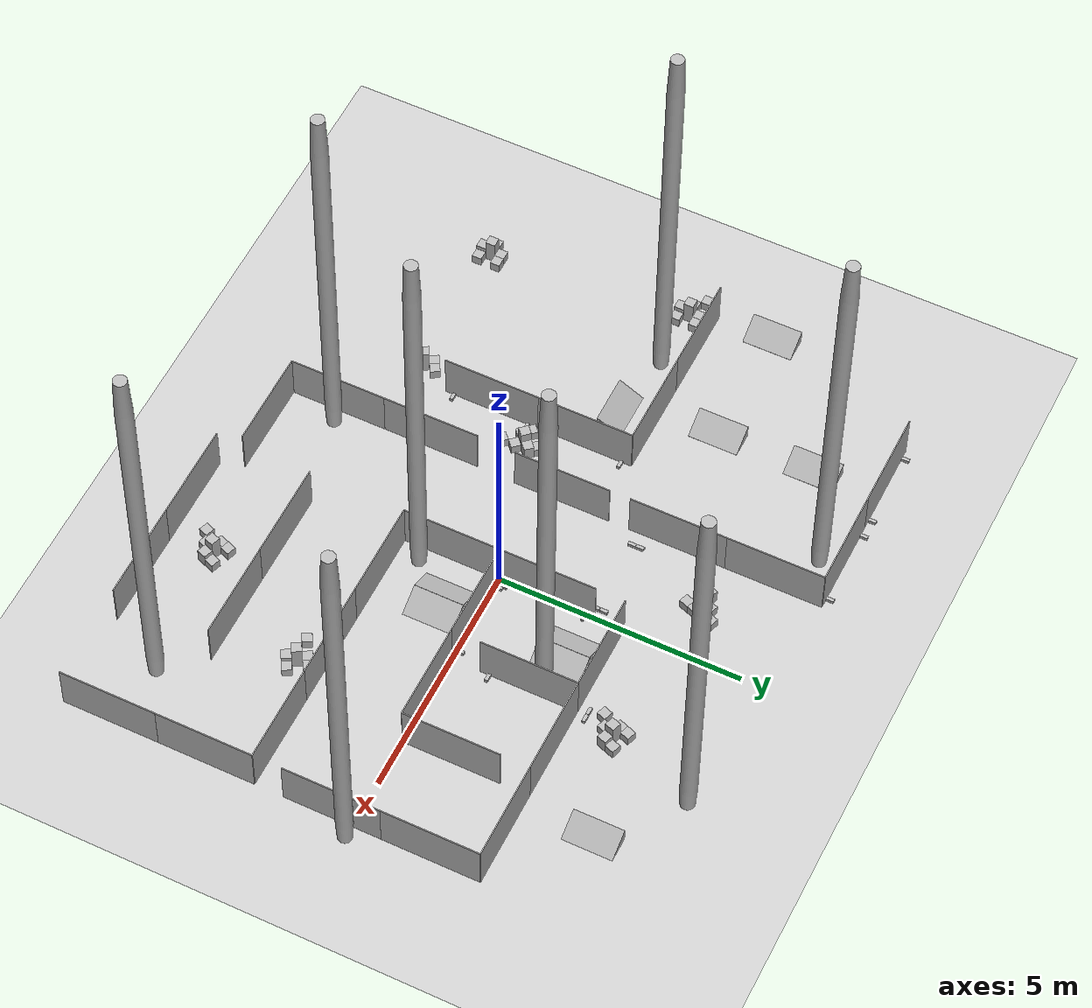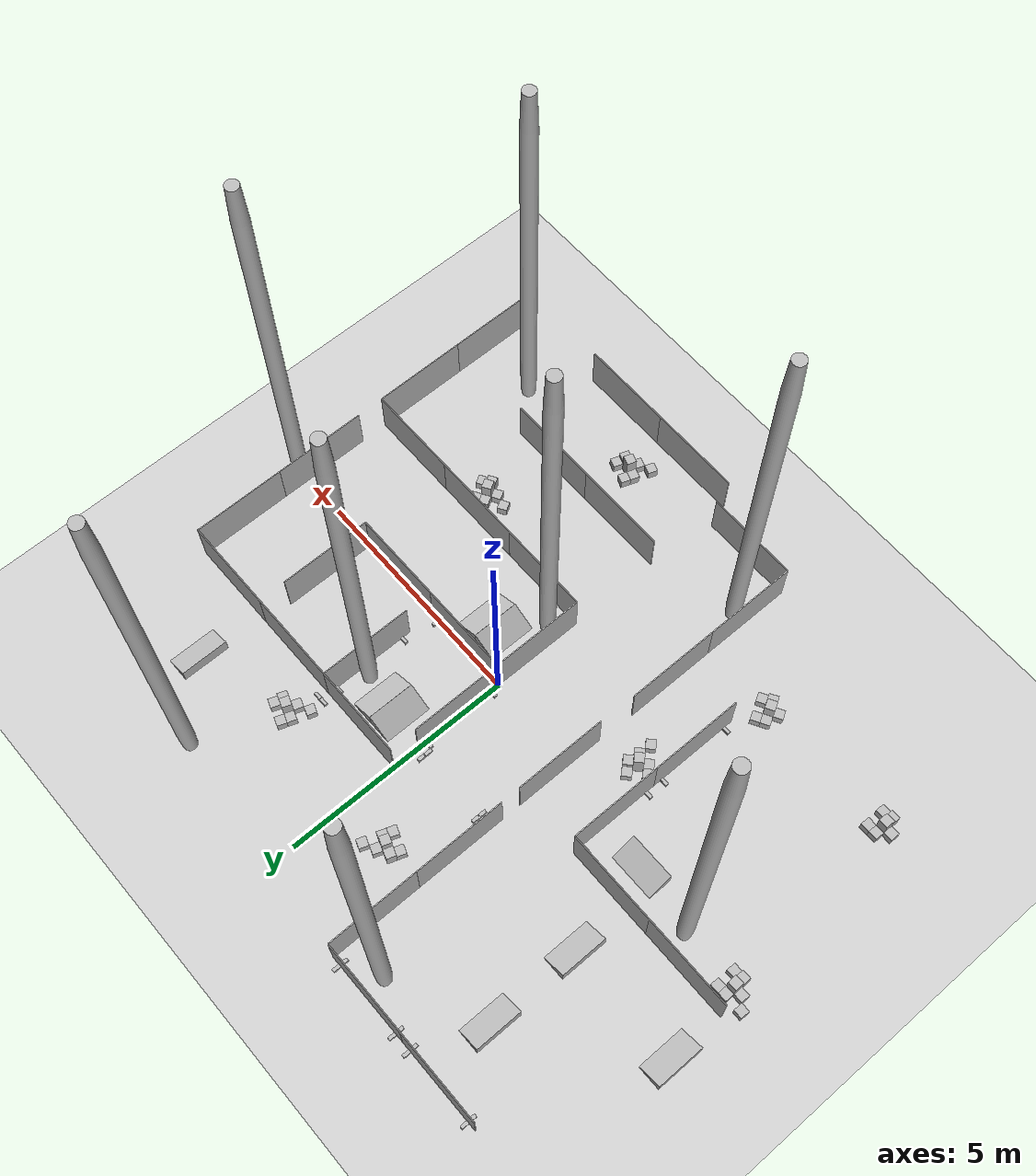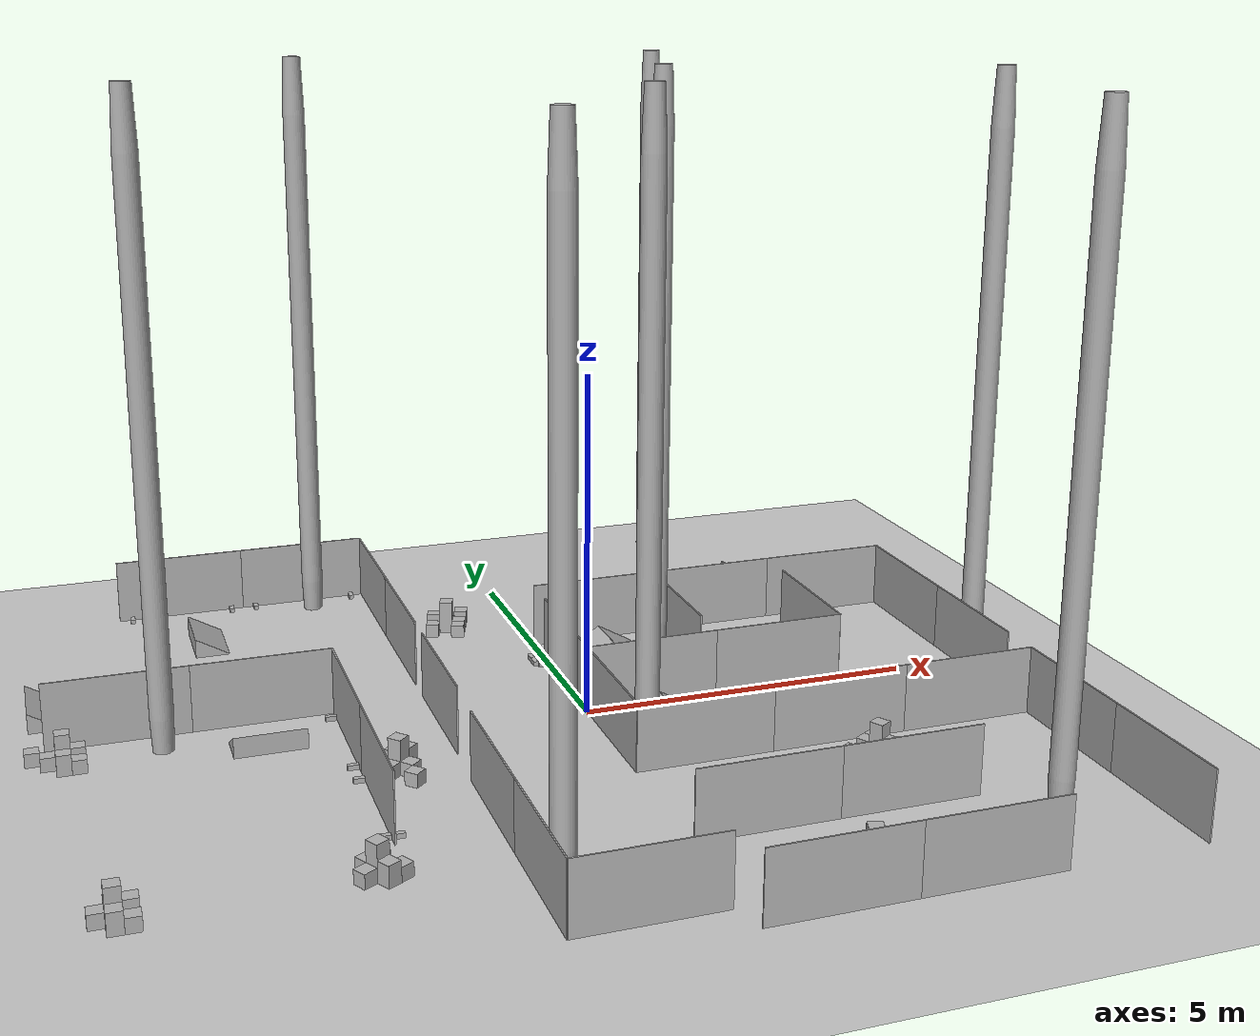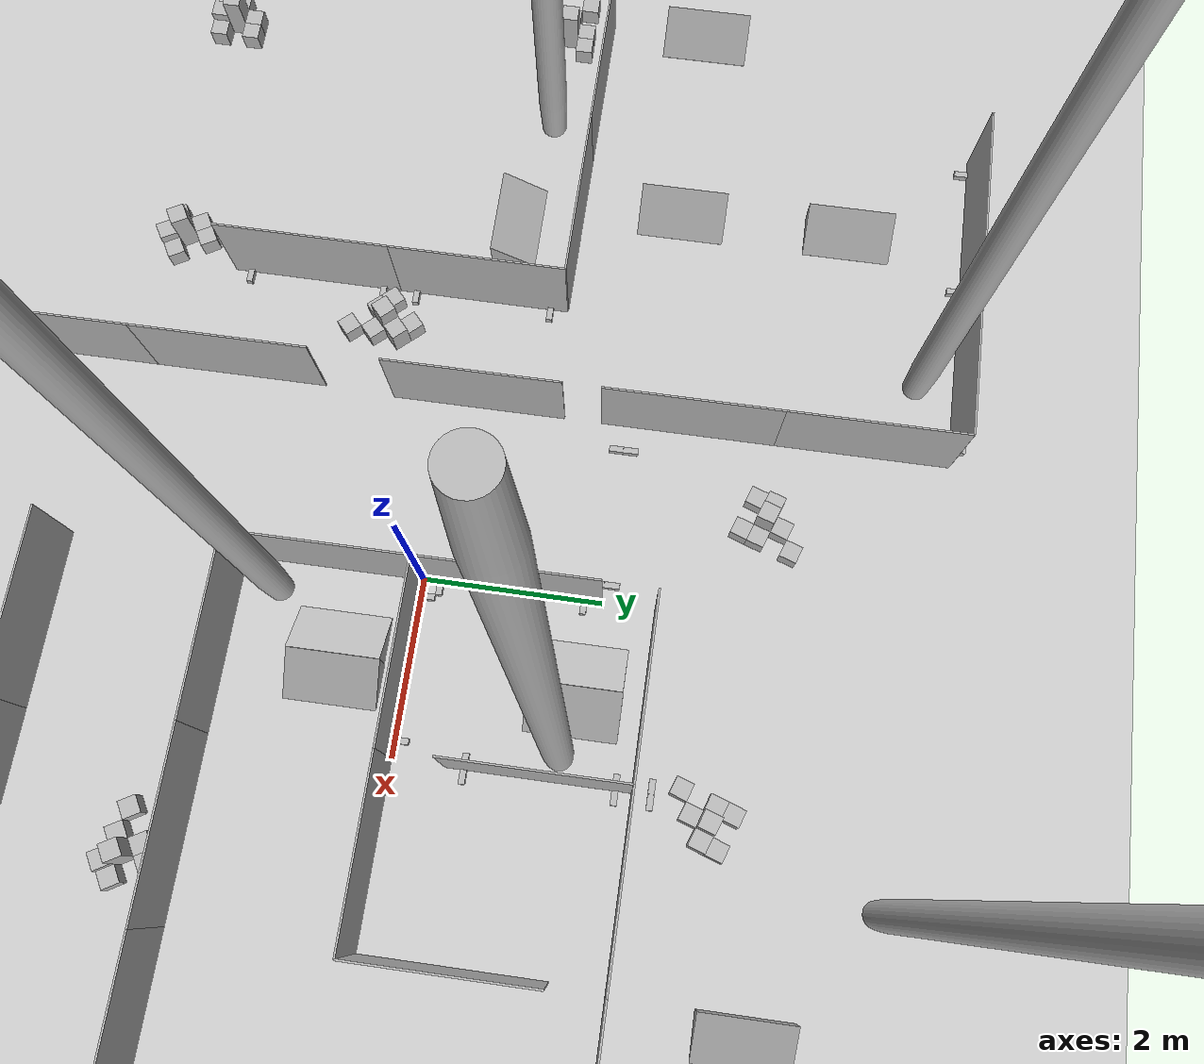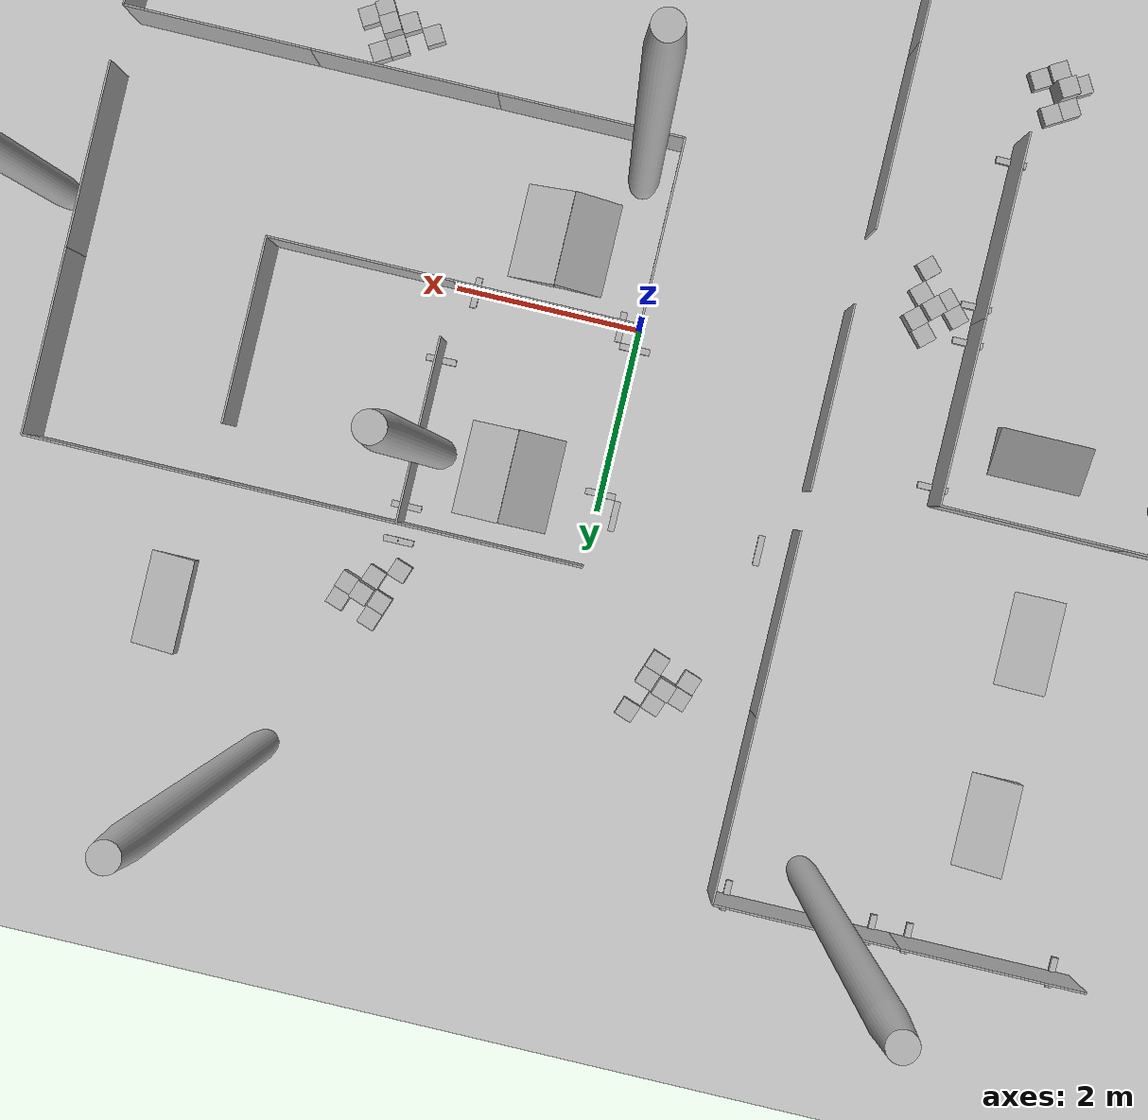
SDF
<sdf version="1.4">
  <!--Generated by blend2world.py-->
  <world name="arena_HKT_6">
    <scene>
      <ambient>0.5 0.5 0.5 1</ambient>
      <background>0.5 0.5 0.5 1</background>
      <shadows>false</shadows>
    </scene>
    <physics type="ode">
      <gravity>0 0 -9.81</gravity>
      <ode>
        <solver>
          <type>quick</type>
          <iters>1000</iters>
          <sor>1.3</sor>
        </solver>
        <constraints>
          <cfm>0.0</cfm>
          <erp>0.2</erp>
          <contact_max_correcting_vel>100.0</contact_max_correcting_vel>
          <contact_surface_layer>0.001</contact_surface_layer>
        </constraints>
      </ode>
      <real_time_update_rate>120</real_time_update_rate>
      <real_time_factor>1</real_time_factor>
      <max_step_size>0.008333</max_step_size>
    </physics>
    <light name="directional_light_1" type="directional">
      <cast_shadows>false</cast_shadows>
      <pose>0 0 30 0.1 0.1 0</pose>
      <diffuse>1.0 1.0 1.0 1</diffuse>
      <specular>.1 .1 .1 1</specular>
      <attenuation>
        <range>300</range>
      </attenuation>
      <direction>0.1 0.1 -1</direction>
    </light>
    <include>
      <uri>model://ground_plane</uri>
    </include>
    <light name="directional_light.-10.0_-12.0" type="sun">
      <pose>-10.0 -12.0 8  0 0 0</pose>
      <cast_shadows>1</cast_shadows>
      <diffuse>0.5 0.5 0.5 1</diffuse>
      <specular>0.1 0.1 0.1 1</specular>
      <attenuation>
        <range>20</range>
        <constant>0.5</constant>
        <linear>0.01</linear>
        <quadratic>0.00</quadratic>
      </attenuation>
      <direction>0.1 0.1 -1.0</direction>
    </light>
    <light name="directional_light.-10.0_0.0" type="sun">
      <pose>-10.0 0.0 8  0 0 0</pose>
      <cast_shadows>1</cast_shadows>
      <diffuse>0.5 0.5 0.5 1</diffuse>
      <specular>0.1 0.1 0.1 1</specular>
      <attenuation>
        <range>20</range>
        <constant>0.5</constant>
        <linear>0.01</linear>
        <quadratic>0.00</quadratic>
      </attenuation>
      <direction>0.1 0.1 -1.0</direction>
    </light>
    <light name="directional_light.-10.0_12.0" type="sun">
      <pose>-10.0 12.0 8  0 0 0</pose>
      <cast_shadows>1</cast_shadows>
      <diffuse>0.5 0.5 0.5 1</diffuse>
      <specular>0.1 0.1 0.1 1</specular>
      <attenuation>
        <range>20</range>
        <constant>0.5</constant>
        <linear>0.01</linear>
        <quadratic>0.00</quadratic>
      </attenuation>
      <direction>0.1 0.1 -1.0</direction>
    </light>
    <light name="directional_light.0.0_-12.0" type="sun">
      <pose>0.0 -12.0 8  0 0 0</pose>
      <cast_shadows>1</cast_shadows>
      <diffuse>0.5 0.5 0.5 1</diffuse>
      <specular>0.1 0.1 0.1 1</specular>
      <attenuation>
        <range>20</range>
        <constant>0.5</constant>
        <linear>0.01</linear>
        <quadratic>0.00</quadratic>
      </attenuation>
      <direction>0.1 0.1 -1.0</direction>
    </light>
    <light name="directional_light.0.0_0.0" type="sun">
      <pose>0.0 0.0 8  0 0 0</pose>
      <cast_shadows>1</cast_shadows>
      <diffuse>0.5 0.5 0.5 1</diffuse>
      <specular>0.1 0.1 0.1 1</specular>
      <attenuation>
        <range>20</range>
        <constant>0.5</constant>
        <linear>0.01</linear>
        <quadratic>0.00</quadratic>
      </attenuation>
      <direction>0.1 0.1 -1.0</direction>
    </light>
    <light name="directional_light.0.0_12.0" type="sun">
      <pose>0.0 12.0 8  0 0 0</pose>
      <cast_shadows>1</cast_shadows>
      <diffuse>0.5 0.5 0.5 1</diffuse>
      <specular>0.1 0.1 0.1 1</specular>
      <attenuation>
        <range>20</range>
        <constant>0.5</constant>
        <linear>0.01</linear>
        <quadratic>0.00</quadratic>
      </attenuation>
      <direction>0.1 0.1 -1.0</direction>
    </light>
    <light name="directional_light.10.0_-12.0" type="sun">
      <pose>10.0 -12.0 8  0 0 0</pose>
      <cast_shadows>1</cast_shadows>
      <diffuse>0.5 0.5 0.5 1</diffuse>
      <specular>0.1 0.1 0.1 1</specular>
      <attenuation>
        <range>20</range>
        <constant>0.5</constant>
        <linear>0.01</linear>
        <quadratic>0.00</quadratic>
      </attenuation>
      <direction>0.1 0.1 -1.0</direction>
    </light>
    <light name="directional_light.10.0_0.0" type="sun">
      <pose>10.0 0.0 8  0 0 0</pose>
      <cast_shadows>1</cast_shadows>
      <diffuse>0.5 0.5 0.5 1</diffuse>
      <specular>0.1 0.1 0.1 1</specular>
      <attenuation>
        <range>20</range>
        <constant>0.5</constant>
        <linear>0.01</linear>
        <quadratic>0.00</quadratic>
      </attenuation>
      <direction>0.1 0.1 -1.0</direction>
    </light>
    <light name="directional_light.10.0_12.0" type="sun">
      <pose>10.0 12.0 8  0 0 0</pose>
      <cast_shadows>1</cast_shadows>
      <diffuse>0.5 0.5 0.5 1</diffuse>
      <specular>0.1 0.1 0.1 1</specular>
      <attenuation>
        <range>20</range>
        <constant>0.5</constant>
        <linear>0.01</linear>
        <quadratic>0.00</quadratic>
      </attenuation>
      <direction>0.1 0.1 -1.0</direction>
    </light>
    <include>
      <name>barrel_110l.032</name>
      <pose>-5.915884017944336 0.5900893807411194 0.0  0.0 0.0 0.0</pose>
      <uri>model://barrel_110l</uri>
    </include>
    <include>
      <name>barrel_110l.033</name>
      <pose>-3.0217368602752686 5.237995624542236 0.0  0.0 0.0 0.0</pose>
      <uri>model://barrel_110l</uri>
    </include>
    <include>
      <name>barrel_110l.034</name>
      <pose>2.890841007232666 5.237995624542236 0.0  0.0 0.0 0.0</pose>
      <uri>model://barrel_110l</uri>
    </include>
    <include>
      <name>barrel_110l.035</name>
      <pose>4.665648460388184 -4.783429145812988 0.0  0.0 0.0 0.0</pose>
      <uri>model://barrel_110l</uri>
    </include>
    <include>
      <name>barrel_110l.036</name>
      <pose>0.32114124298095703 -1.5364108085632324 0.0  0.0 0.0 0.0</pose>
      <uri>model://barrel_110l</uri>
    </include>
    <include>
      <name>barrel_110l.037</name>
      <pose>6.263016223907471 -0.004051387310028076 0.0  0.0 0.0 0.0</pose>
      <uri>model://barrel_110l</uri>
    </include>
    <include>
      <name>barrel_110l.038</name>
      <pose>1.745392918586731 1.7787275314331055 0.0  0.0 0.0 0.0</pose>
      <uri>model://barrel_110l</uri>
    </include>
    <include>
      <name>barrel_110l.039</name>
      <pose>-1.8483179807662964 -4.4844746589660645 0.0  0.0 0.0 0.0</pose>
      <uri>model://barrel_110l</uri>
    </include>
    <include>
      <name>cube_20x20.835</name>
      <pose>-7.231788635253906 0.8086726665496826 0.10000000149011612  0.0 -0.0 3.141592502593994</pose>
      <uri>model://cube_20x20</uri>
    </include>
    <include>
      <name>cube_20x20.836</name>
      <pose>-7.431788444519043 0.6086728572845459 0.10000000149011612  0.0 -0.0 3.141592502593994</pose>
      <uri>model://cube_20x20</uri>
    </include>
    <include>
      <name>cube_20x20.837</name>
      <pose>-7.63178825378418 0.8086726665496826 0.10000000149011612  0.0 -0.0 3.141592502593994</pose>
      <uri>model://cube_20x20</uri>
    </include>
    <include>
      <name>cube_20x20.838</name>
      <pose>-7.031788349151611 0.8086726665496826 0.10000000149011612  0.0 -0.0 3.141592502593994</pose>
      <uri>model://cube_20x20</uri>
    </include>
    <include>
      <name>cube_20x20.839</name>
      <pose>-7.031788349151611 0.4086730480194092 0.10000000149011612  0.0 -0.0 3.141592502593994</pose>
      <uri>model://cube_20x20</uri>
    </include>
    <include>
      <name>cube_20x20.840</name>
      <pose>-7.231788635253906 0.8086726665496826 0.10000000149011612  0.0 -0.0 3.141592502593994</pose>
      <uri>model://cube_20x20</uri>
    </include>
    <include>
      <name>cube_20x20.841</name>
      <pose>-7.431788444519043 0.6086728572845459 0.10000000149011612  0.0 -0.0 3.141592502593994</pose>
      <uri>model://cube_20x20</uri>
    </include>
    <include>
      <name>cube_20x20.842</name>
      <pose>-7.63178825378418 0.8086726665496826 0.10000000149011612  0.0 -0.0 3.141592502593994</pose>
      <uri>model://cube_20x20</uri>
    </include>
    <include>
      <name>cube_20x20.843</name>
      <pose>-7.031788349151611 0.8086726665496826 0.10000000149011612  0.0 -0.0 3.141592502593994</pose>
      <uri>model://cube_20x20</uri>
    </include>
    <include>
      <name>cube_20x20.844</name>
      <pose>-7.031788349151611 0.4086730480194092 0.10000000149011612  0.0 -0.0 3.141592502593994</pose>
      <uri>model://cube_20x20</uri>
    </include>
    <include>
      <name>cube_20x20.845</name>
      <pose>-6.874878406524658 -3.3630831241607666 0.10000000149011612  0.0 -0.0 3.141592502593994</pose>
      <uri>model://cube_20x20</uri>
    </include>
    <include>
      <name>cube_20x20.846</name>
      <pose>-7.074878215789795 -3.5630829334259033 0.10000000149011612  0.0 -0.0 3.141592502593994</pose>
      <uri>model://cube_20x20</uri>
    </include>
    <include>
      <name>cube_20x20.847</name>
      <pose>-6.674878120422363 -3.3630831241607666 0.10000000149011612  0.0 -0.0 3.141592502593994</pose>
      <uri>model://cube_20x20</uri>
    </include>
    <include>
      <name>cube_20x20.848</name>
      <pose>-6.674878120422363 -3.76308274269104 0.10000000149011612  0.0 -0.0 3.141592502593994</pose>
      <uri>model://cube_20x20</uri>
    </include>
    <include>
      <name>cube_20x20.849</name>
      <pose>-6.874878406524658 -3.3630831241607666 0.10000000149011612  0.0 -0.0 3.141592502593994</pose>
      <uri>model://cube_20x20</uri>
    </include>
    <include>
      <name>cube_20x20.850</name>
      <pose>-7.074878215789795 -3.5630829334259033 0.10000000149011612  0.0 -0.0 3.141592502593994</pose>
      <uri>model://cube_20x20</uri>
    </include>
    <include>
      <name>cube_20x20.851</name>
      <pose>-6.674878120422363 -3.3630831241607666 0.10000000149011612  0.0 -0.0 3.141592502593994</pose>
      <uri>model://cube_20x20</uri>
    </include>
    <include>
      <name>cube_20x20.852</name>
      <pose>-6.674878120422363 -3.76308274269104 0.10000000149011612  0.0 -0.0 3.141592502593994</pose>
      <uri>model://cube_20x20</uri>
    </include>
    <include>
      <name>cube_20x20.853</name>
      <pose>-3.9385533332824707 -3.3717634677886963 0.10000000149011612  0.0 -0.0 3.6651763916015625</pose>
      <uri>model://cube_20x20</uri>
    </include>
    <include>
      <name>cube_20x20.854</name>
      <pose>-4.011762619018555 -3.6449673175811768 0.10000000149011612  0.0 -0.0 3.6651763916015625</pose>
      <uri>model://cube_20x20</uri>
    </include>
    <include>
      <name>cube_20x20.855</name>
      <pose>-3.7653465270996094 -3.271765947341919 0.10000000149011612  0.0 -0.0 3.6651763916015625</pose>
      <uri>model://cube_20x20</uri>
    </include>
    <include>
      <name>cube_20x20.856</name>
      <pose>-3.565351963043213 -3.6181790828704834 0.10000000149011612  0.0 -0.0 3.6651763916015625</pose>
      <uri>model://cube_20x20</uri>
    </include>
    <include>
      <name>cube_20x20.857</name>
      <pose>-3.9385533332824707 -3.3717634677886963 0.10000000149011612  0.0 -0.0 3.6651763916015625</pose>
      <uri>model://cube_20x20</uri>
    </include>
    <include>
      <name>cube_20x20.858</name>
      <pose>-4.011762619018555 -3.6449673175811768 0.10000000149011612  0.0 -0.0 3.6651763916015625</pose>
      <uri>model://cube_20x20</uri>
    </include>
    <include>
      <name>cube_20x20.859</name>
      <pose>-3.7653465270996094 -3.271765947341919 0.10000000149011612  0.0 -0.0 3.6651763916015625</pose>
      <uri>model://cube_20x20</uri>
    </include>
    <include>
      <name>cube_20x20.860</name>
      <pose>-3.565351963043213 -3.6181790828704834 0.10000000149011612  0.0 -0.0 3.6651763916015625</pose>
      <uri>model://cube_20x20</uri>
    </include>
    <include>
      <name>cube_20x20.861</name>
      <pose>-3.1368727684020996 -1.071094274520874 0.10000000149011612  0.0 0.0 5.4528021812438965</pose>
      <uri>model://cube_20x20</uri>
    </include>
    <include>
      <name>cube_20x20.862</name>
      <pose>-2.8543167114257812 -1.0838134288787842 0.10000000149011612  0.0 0.0 5.4528021812438965</pose>
      <uri>model://cube_20x20</uri>
    </include>
    <include>
      <name>cube_20x20.863</name>
      <pose>-2.8670363426208496 -1.3663697242736816 0.10000000149011612  0.0 0.0 5.4528021812438965</pose>
      <uri>model://cube_20x20</uri>
    </include>
    <include>
      <name>cube_20x20.864</name>
      <pose>-3.2717912197113037 -0.9234559535980225 0.10000000149011612  0.0 0.0 5.4528021812438965</pose>
      <uri>model://cube_20x20</uri>
    </include>
    <include>
      <name>cube_20x20.865</name>
      <pose>-2.976515293121338 -0.6536192893981934 0.10000000149011612  0.0 0.0 5.4528021812438965</pose>
      <uri>model://cube_20x20</uri>
    </include>
    <include>
      <name>cube_20x20.866</name>
      <pose>-3.1368727684020996 -1.071094274520874 0.10000000149011612  0.0 0.0 5.4528021812438965</pose>
      <uri>model://cube_20x20</uri>
    </include>
    <include>
      <name>cube_20x20.867</name>
      <pose>-2.8543167114257812 -1.0838134288787842 0.10000000149011612  0.0 0.0 5.4528021812438965</pose>
      <uri>model://cube_20x20</uri>
    </include>
    <include>
      <name>cube_20x20.868</name>
      <pose>-2.8670363426208496 -1.3663697242736816 0.10000000149011612  0.0 0.0 5.4528021812438965</pose>
      <uri>model://cube_20x20</uri>
    </include>
    <include>
      <name>cube_20x20.869</name>
      <pose>-3.2717912197113037 -0.9234559535980225 0.10000000149011612  0.0 0.0 5.4528021812438965</pose>
      <uri>model://cube_20x20</uri>
    </include>
    <include>
      <name>cube_20x20.870</name>
      <pose>-2.976515293121338 -0.6536192893981934 0.10000000149011612  0.0 0.0 5.4528021812438965</pose>
      <uri>model://cube_20x20</uri>
    </include>
    <include>
      <name>cube_20x30.135</name>
      <pose>-7.231788635253906 0.4086730480194092 0.15000000596046448  0.0 -0.0 3.141592502593994</pose>
      <uri>model://cube_20x30</uri>
    </include>
    <include>
      <name>cube_20x30.136</name>
      <pose>-7.231788635253906 0.4086730480194092 0.15000000596046448  0.0 -0.0 3.141592502593994</pose>
      <uri>model://cube_20x30</uri>
    </include>
    <include>
      <name>cube_20x30.137</name>
      <pose>-6.874878406524658 -3.76308274269104 0.15000000596046448  0.0 -0.0 3.141592502593994</pose>
      <uri>model://cube_20x30</uri>
    </include>
    <include>
      <name>cube_20x30.138</name>
      <pose>-6.874878406524658 -3.76308274269104 0.15000000596046448  0.0 -0.0 3.141592502593994</pose>
      <uri>model://cube_20x30</uri>
    </include>
    <include>
      <name>cube_20x30.139</name>
      <pose>-3.738558769226074 -3.7181766033172607 0.15000000596046448  0.0 -0.0 3.6651763916015625</pose>
      <uri>model://cube_20x30</uri>
    </include>
    <include>
      <name>cube_20x30.140</name>
      <pose>-3.738558769226074 -3.7181766033172607 0.15000000596046448  0.0 -0.0 3.6651763916015625</pose>
      <uri>model://cube_20x30</uri>
    </include>
    <include>
      <name>cube_20x30.141</name>
      <pose>-2.841596841812134 -0.8012573719024658 0.15000000596046448  0.0 0.0 5.4528021812438965</pose>
      <uri>model://cube_20x30</uri>
    </include>
    <include>
      <name>cube_20x30.142</name>
      <pose>-2.841596841812134 -0.8012573719024658 0.15000000596046448  0.0 0.0 5.4528021812438965</pose>
      <uri>model://cube_20x30</uri>
    </include>
    <include>
      <name>cube_20x50.129</name>
      <pose>-7.231788635253906 0.6086728572845459 0.25  0.0 -0.0 3.141592502593994</pose>
      <uri>model://cube_20x50</uri>
    </include>
    <include>
      <name>cube_20x50.130</name>
      <pose>-7.231788635253906 0.6086728572845459 0.25  0.0 -0.0 3.141592502593994</pose>
      <uri>model://cube_20x50</uri>
    </include>
    <include>
      <name>cube_20x50.131</name>
      <pose>-6.874878406524658 -3.5630829334259033 0.25  0.0 -0.0 3.141592502593994</pose>
      <uri>model://cube_20x50</uri>
    </include>
    <include>
      <name>cube_20x50.132</name>
      <pose>-6.874878406524658 -3.5630829334259033 0.25  0.0 -0.0 3.141592502593994</pose>
      <uri>model://cube_20x50</uri>
    </include>
    <include>
      <name>cube_20x50.133</name>
      <pose>-3.8385560512542725 -3.5449702739715576 0.25  0.0 -0.0 3.6651763916015625</pose>
      <uri>model://cube_20x50</uri>
    </include>
    <include>
      <name>cube_20x50.134</name>
      <pose>-3.8385560512542725 -3.5449702739715576 0.25  0.0 -0.0 3.6651763916015625</pose>
      <uri>model://cube_20x50</uri>
    </include>
    <include>
      <name>cube_20x50.135</name>
      <pose>-2.989234209060669 -0.9361758232116699 0.25  0.0 0.0 5.4528021812438965</pose>
      <uri>model://cube_20x50</uri>
    </include>
    <include>
      <name>cube_20x50.136</name>
      <pose>-2.989234209060669 -0.9361758232116699 0.25  0.0 0.0 5.4528021812438965</pose>
      <uri>model://cube_20x50</uri>
    </include>
    <include>
      <name>ramp.041</name>
      <pose>-4.520613670349121 0.37118804454803467 0.15000000596046448  0.0 -0.0 7.853981971740723</pose>
      <uri>model://ramp</uri>
    </include>
    <include>
      <name>ramp.042</name>
      <pose>-7.408809661865234 2.3036534786224365 0.15000000596046448  0.0 -0.0 6.283185005187988</pose>
      <uri>model://ramp</uri>
    </include>
    <include>
      <name>ramp.043</name>
      <pose>-4.8568115234375 2.3036534786224365 0.15000000596046448  0.0 -0.0 6.283185005187988</pose>
      <uri>model://ramp</uri>
    </include>
    <include>
      <name>ramp.044</name>
      <pose>-4.8568115234375 4.303653717041016 0.15000000596046448  0.0 -0.0 6.283185005187988</pose>
      <uri>model://ramp</uri>
    </include>
    <include>
      <name>wall_2x1.317</name>
      <pose>-3.476762056350708 -1.890228271484375 0.5130000114440918  0.0 -0.0 4.708364486694336</pose>
      <uri>model://wall_2x1</uri>
    </include>
    <include>
      <name>wall_2x1.318</name>
      <pose>-6.464663505554199 1.1218221187591553 0.5130000114440918  0.0 -0.0 3.1375677585601807</pose>
      <uri>model://wall_2x1</uri>
    </include>
    <include>
      <name>wall_stand.722</name>
      <pose>-1.8005000352859497 2.0 0.03449999913573265  0.0 -0.0 1.570796251296997</pose>
      <uri>model://wall_stand</uri>
    </include>
    <include>
      <name>wall_stand.723</name>
      <pose>-0.19949999451637268 2.0 0.03449999913573265  0.0 -0.0 1.570796251296997</pose>
      <uri>model://wall_stand</uri>
    </include>
    <include>
      <name>wall_2x1.319</name>
      <pose>-3.468712091445923 0.1097555160522461 0.5130000114440918  0.0 -0.0 4.708364486694336</pose>
      <uri>model://wall_2x1</uri>
    </include>
    <include>
      <name>wall_2x1.320</name>
      <pose>-4.464678764343262 1.1137723922729492 0.5130000114440918  0.0 -0.0 3.1375677585601807</pose>
      <uri>model://wall_2x1</uri>
    </include>
    <include>
      <name>wall_stand.724</name>
      <pose>-0.19949999451637268 2.0 0.03449999913573265  0.0 -0.0 1.570796251296997</pose>
      <uri>model://wall_stand</uri>
    </include>
    <include>
      <name>wall_2x1.321</name>
      <pose>-2.147331953048706 -2.5302858352661133 0.5130000114440918  0.0 -0.0 1.570796251296997</pose>
      <uri>model://wall_2x1</uri>
    </include>
    <include>
      <name>wall_stand.725</name>
      <pose>-1.8005000352859497 2.0 0.03449999913573265  0.0 -0.0 1.570796251296997</pose>
      <uri>model://wall_stand</uri>
    </include>
    <include>
      <name>wall_stand.726</name>
      <pose>-0.19949999451637268 2.0 0.03449999913573265  0.0 -0.0 1.570796251296997</pose>
      <uri>model://wall_stand</uri>
    </include>
    <include>
      <name>wall_2x1.322</name>
      <pose>-1.1473321914672852 -5.530285835266113 0.5130000114440918  0.0 -0.0 3.141592502593994</pose>
      <uri>model://wall_2x1</uri>
    </include>
    <include>
      <name>wall_2x1.323</name>
      <pose>-2.147332191467285 -4.530285835266113 0.5130000114440918  0.0 -0.0 1.570796251296997</pose>
      <uri>model://wall_2x1</uri>
    </include>
    <include>
      <name>wall_stand.727</name>
      <pose>-0.19949999451637268 2.0 0.03449999913573265  0.0 -0.0 1.570796251296997</pose>
      <uri>model://wall_stand</uri>
    </include>
    <include>
      <name>wall_2x1.324</name>
      <pose>-2.1166141033172607 2.695002794265747 0.5130000114440918  0.0 -0.0 4.71238899230957</pose>
      <uri>model://wall_2x1</uri>
    </include>
    <include>
      <name>wall_stand.728</name>
      <pose>-1.8005000352859497 2.0 0.03449999913573265  0.0 -0.0 1.570796251296997</pose>
      <uri>model://wall_stand</uri>
    </include>
    <include>
      <name>wall_stand.729</name>
      <pose>-0.19949999451637268 2.0 0.03449999913573265  0.0 -0.0 1.570796251296997</pose>
      <uri>model://wall_stand</uri>
    </include>
    <include>
      <name>wall_2x1.325</name>
      <pose>-5.116613388061523 5.695002555847168 0.5130000114440918  0.0 -0.0 6.283185005187988</pose>
      <uri>model://wall_2x1</uri>
    </include>
    <include>
      <name>wall_2x1.326</name>
      <pose>-3.1166136264801025 5.695002555847168 0.5130000114440918  0.0 -0.0 6.283185005187988</pose>
      <uri>model://wall_2x1</uri>
    </include>
    <include>
      <name>wall_2x1.327</name>
      <pose>-2.1166136264801025 4.695002555847168 0.5130000114440918  0.0 -0.0 4.71238899230957</pose>
      <uri>model://wall_2x1</uri>
    </include>
    <include>
      <name>wall_stand.730</name>
      <pose>-0.19949999451637268 2.0 0.03449999913573265  0.0 -0.0 1.570796251296997</pose>
      <uri>model://wall_stand</uri>
    </include>
    <include>
      <name>wall_2x1.328</name>
      <pose>-2.1166141033172607 0.2739219665527344 0.5130000114440918  0.0 -0.0 4.71238899230957</pose>
      <uri>model://wall_2x1</uri>
    </include>
    <include>
      <name>wall_stand.731</name>
      <pose>-1.8005000352859497 2.0 0.03449999913573265  0.0 -0.0 1.570796251296997</pose>
      <uri>model://wall_stand</uri>
    </include>
    <include>
      <name>wall_stand.732</name>
      <pose>-0.19949999451637268 2.0 0.03449999913573265  0.0 -0.0 1.570796251296997</pose>
      <uri>model://wall_stand</uri>
    </include>
    <include>
      <name>wall_stand.733</name>
      <pose>-3.4799840450286865 -2.6907219886779785 0.03450000286102295  0.0 -0.0 3.1375677585601807</pose>
      <uri>model://wall_stand</uri>
    </include>
    <include>
      <name>wall_stand.734</name>
      <pose>-3.4735400676727295 -1.0897347927093506 0.03450000286102295  0.0 -0.0 3.1375677585601807</pose>
      <uri>model://wall_stand</uri>
    </include>
    <include>
      <name>wall_stand.735</name>
      <pose>-3.4719340801239014 -0.6907380819320679 0.03450000286102295  0.0 -0.0 3.1375677585601807</pose>
      <uri>model://wall_stand</uri>
    </include>
    <include>
      <name>wall_stand.736</name>
      <pose>-3.4654901027679443 0.9102489948272705 0.03450000286102295  0.0 -0.0 3.1375677585601807</pose>
      <uri>model://wall_stand</uri>
    </include>
    <include>
      <name>wall_stand.738</name>
      <pose>-5.917113304138184 5.695002555847168 0.03450000286102295  0.0 -0.0 4.71238899230957</pose>
      <uri>model://wall_stand</uri>
    </include>
    <include>
      <name>wall_stand.739</name>
      <pose>-4.316113471984863 5.695002555847168 0.03450000286102295  0.0 -0.0 4.71238899230957</pose>
      <uri>model://wall_stand</uri>
    </include>
    <include>
      <name>wall_stand.740</name>
      <pose>-2.316113233566284 5.695002555847168 0.03450000286102295  0.0 -0.0 4.71238899230957</pose>
      <uri>model://wall_stand</uri>
    </include>
    <include>
      <name>wall_stand.741</name>
      <pose>-3.9171135425567627 5.695002555847168 0.03450000286102295  0.0 -0.0 4.71238899230957</pose>
      <uri>model://wall_stand</uri>
    </include>
    <include>
      <name>cube_20x20.871</name>
      <pose>2.0343916416168213 3.479175329208374 0.10000000149011612  0.0 0.0 4.376082897186279</pose>
      <uri>model://cube_20x20</uri>
    </include>
    <include>
      <name>cube_20x20.872</name>
      <pose>2.1571874618530273 3.224379301071167 0.10000000149011612  0.0 0.0 4.376082897186279</pose>
      <uri>model://cube_20x20</uri>
    </include>
    <include>
      <name>cube_20x20.873</name>
      <pose>1.902390956878662 3.1015841960906982 0.10000000149011612  0.0 0.0 4.376082897186279</pose>
      <uri>model://cube_20x20</uri>
    </include>
    <include>
      <name>cube_20x20.874</name>
      <pose>2.1003925800323486 3.66797137260437 0.10000000149011612  0.0 0.0 4.376082897186279</pose>
      <uri>model://cube_20x20</uri>
    </include>
    <include>
      <name>cube_20x20.875</name>
      <pose>2.4779841899871826 3.535970449447632 0.10000000149011612  0.0 0.0 4.376082897186279</pose>
      <uri>model://cube_20x20</uri>
    </include>
    <include>
      <name>cube_20x20.876</name>
      <pose>2.0343916416168213 3.479175329208374 0.10000000149011612  0.0 0.0 4.376082897186279</pose>
      <uri>model://cube_20x20</uri>
    </include>
    <include>
      <name>cube_20x20.877</name>
      <pose>2.1571874618530273 3.224379301071167 0.10000000149011612  0.0 0.0 4.376082897186279</pose>
      <uri>model://cube_20x20</uri>
    </include>
    <include>
      <name>cube_20x20.878</name>
      <pose>1.902390956878662 3.1015841960906982 0.10000000149011612  0.0 0.0 4.376082897186279</pose>
      <uri>model://cube_20x20</uri>
    </include>
    <include>
      <name>cube_20x20.879</name>
      <pose>2.1003925800323486 3.66797137260437 0.10000000149011612  0.0 0.0 4.376082897186279</pose>
      <uri>model://cube_20x20</uri>
    </include>
    <include>
      <name>cube_20x20.880</name>
      <pose>2.4779841899871826 3.535970449447632 0.10000000149011612  0.0 0.0 4.376082897186279</pose>
      <uri>model://cube_20x20</uri>
    </include>
    <include>
      <name>cube_20x20.881</name>
      <pose>-0.9480915069580078 3.6092355251312256 0.10000000149011612  0.0 0.0 7.517675399780273</pose>
      <uri>model://cube_20x20</uri>
    </include>
    <include>
      <name>cube_20x20.882</name>
      <pose>-1.0708873271942139 3.8640315532684326 0.10000000149011612  0.0 0.0 7.517675399780273</pose>
      <uri>model://cube_20x20</uri>
    </include>
    <include>
      <name>cube_20x20.883</name>
      <pose>-0.8160908222198486 3.9868276119232178 0.10000000149011612  0.0 0.0 7.517675399780273</pose>
      <uri>model://cube_20x20</uri>
    </include>
    <include>
      <name>cube_20x20.884</name>
      <pose>-1.0140924453735352 3.4204394817352295 0.10000000149011612  0.0 0.0 7.517675399780273</pose>
      <uri>model://cube_20x20</uri>
    </include>
    <include>
      <name>cube_20x20.885</name>
      <pose>-1.3916840553283691 3.5524404048919678 0.10000000149011612  0.0 0.0 7.517675399780273</pose>
      <uri>model://cube_20x20</uri>
    </include>
    <include>
      <name>cube_20x20.886</name>
      <pose>-0.9480915069580078 3.6092355251312256 0.10000000149011612  0.0 0.0 7.517675399780273</pose>
      <uri>model://cube_20x20</uri>
    </include>
    <include>
      <name>cube_20x20.887</name>
      <pose>-1.0708873271942139 3.8640315532684326 0.10000000149011612  0.0 0.0 7.517675399780273</pose>
      <uri>model://cube_20x20</uri>
    </include>
    <include>
      <name>cube_20x20.888</name>
      <pose>-0.8160908222198486 3.9868276119232178 0.10000000149011612  0.0 0.0 7.517675399780273</pose>
      <uri>model://cube_20x20</uri>
    </include>
    <include>
      <name>cube_20x20.889</name>
      <pose>-1.0140924453735352 3.4204394817352295 0.10000000149011612  0.0 0.0 7.517675399780273</pose>
      <uri>model://cube_20x20</uri>
    </include>
    <include>
      <name>cube_20x20.890</name>
      <pose>-1.3916840553283691 3.5524404048919678 0.10000000149011612  0.0 0.0 7.517675399780273</pose>
      <uri>model://cube_20x20</uri>
    </include>
    <include>
      <name>cube_20x20.891</name>
      <pose>3.2194247245788574 -2.3717634677886963 0.10000000149011612  0.0 -0.0 3.6651763916015625</pose>
      <uri>model://cube_20x20</uri>
    </include>
    <include>
      <name>cube_20x20.892</name>
      <pose>3.1462156772613525 -2.6449673175811768 0.10000000149011612  0.0 -0.0 3.6651763916015625</pose>
      <uri>model://cube_20x20</uri>
    </include>
    <include>
      <name>cube_20x20.893</name>
      <pose>2.873011827468872 -2.5717580318450928 0.10000000149011612  0.0 -0.0 3.6651763916015625</pose>
      <uri>model://cube_20x20</uri>
    </include>
    <include>
      <name>cube_20x20.894</name>
      <pose>3.3926315307617188 -2.271765947341919 0.10000000149011612  0.0 -0.0 3.6651763916015625</pose>
      <uri>model://cube_20x20</uri>
    </include>
    <include>
      <name>cube_20x20.895</name>
      <pose>3.5926260948181152 -2.6181790828704834 0.10000000149011612  0.0 -0.0 3.6651763916015625</pose>
      <uri>model://cube_20x20</uri>
    </include>
    <include>
      <name>cube_20x20.896</name>
      <pose>3.2194247245788574 -2.3717634677886963 0.10000000149011612  0.0 -0.0 3.6651763916015625</pose>
      <uri>model://cube_20x20</uri>
    </include>
    <include>
      <name>cube_20x20.897</name>
      <pose>3.1462156772613525 -2.6449673175811768 0.10000000149011612  0.0 -0.0 3.6651763916015625</pose>
      <uri>model://cube_20x20</uri>
    </include>
    <include>
      <name>cube_20x20.898</name>
      <pose>2.873011827468872 -2.5717580318450928 0.10000000149011612  0.0 -0.0 3.6651763916015625</pose>
      <uri>model://cube_20x20</uri>
    </include>
    <include>
      <name>cube_20x20.899</name>
      <pose>3.3926315307617188 -2.271765947341919 0.10000000149011612  0.0 -0.0 3.6651763916015625</pose>
      <uri>model://cube_20x20</uri>
    </include>
    <include>
      <name>cube_20x20.900</name>
      <pose>3.5926260948181152 -2.6181790828704834 0.10000000149011612  0.0 -0.0 3.6651763916015625</pose>
      <uri>model://cube_20x20</uri>
    </include>
    <include>
      <name>cube_20x20.901</name>
      <pose>1.691523790359497 -5.038193702697754 0.10000000149011612  0.0 0.0 4.376082897186279</pose>
      <uri>model://cube_20x20</uri>
    </include>
    <include>
      <name>cube_20x20.902</name>
      <pose>1.8143196105957031 -5.292989730834961 0.10000000149011612  0.0 0.0 4.376082897186279</pose>
      <uri>model://cube_20x20</uri>
    </include>
    <include>
      <name>cube_20x20.903</name>
      <pose>1.559523105621338 -5.415785789489746 0.10000000149011612  0.0 0.0 4.376082897186279</pose>
      <uri>model://cube_20x20</uri>
    </include>
    <include>
      <name>cube_20x20.904</name>
      <pose>1.7575247287750244 -4.849397659301758 0.10000000149011612  0.0 0.0 4.376082897186279</pose>
      <uri>model://cube_20x20</uri>
    </include>
    <include>
      <name>cube_20x20.905</name>
      <pose>2.1351163387298584 -4.981398582458496 0.10000000149011612  0.0 0.0 4.376082897186279</pose>
      <uri>model://cube_20x20</uri>
    </include>
    <include>
      <name>cube_20x20.906</name>
      <pose>1.691523790359497 -5.038193702697754 0.10000000149011612  0.0 0.0 4.376082897186279</pose>
      <uri>model://cube_20x20</uri>
    </include>
    <include>
      <name>cube_20x20.907</name>
      <pose>1.8143196105957031 -5.292989730834961 0.10000000149011612  0.0 0.0 4.376082897186279</pose>
      <uri>model://cube_20x20</uri>
    </include>
    <include>
      <name>cube_20x20.908</name>
      <pose>1.559523105621338 -5.415785789489746 0.10000000149011612  0.0 0.0 4.376082897186279</pose>
      <uri>model://cube_20x20</uri>
    </include>
    <include>
      <name>cube_20x20.909</name>
      <pose>1.7575247287750244 -4.849397659301758 0.10000000149011612  0.0 0.0 4.376082897186279</pose>
      <uri>model://cube_20x20</uri>
    </include>
    <include>
      <name>cube_20x20.910</name>
      <pose>2.1351163387298584 -4.981398582458496 0.10000000149011612  0.0 0.0 4.376082897186279</pose>
      <uri>model://cube_20x20</uri>
    </include>
    <include>
      <name>cube_20x30.143</name>
      <pose>2.4119834899902344 3.3471744060516357 0.15000000596046448  0.0 0.0 4.376082897186279</pose>
      <uri>model://cube_20x30</uri>
    </include>
    <include>
      <name>cube_20x30.144</name>
      <pose>2.4119834899902344 3.3471744060516357 0.15000000596046448  0.0 0.0 4.376082897186279</pose>
      <uri>model://cube_20x30</uri>
    </include>
    <include>
      <name>cube_20x30.145</name>
      <pose>-1.325683355331421 3.7412374019622803 0.15000000596046448  0.0 0.0 7.517675399780273</pose>
      <uri>model://cube_20x30</uri>
    </include>
    <include>
      <name>cube_20x30.146</name>
      <pose>-1.325683355331421 3.7412374019622803 0.15000000596046448  0.0 0.0 7.517675399780273</pose>
      <uri>model://cube_20x30</uri>
    </include>
    <include>
      <name>cube_20x30.147</name>
      <pose>3.419419288635254 -2.7181766033172607 0.15000000596046448  0.0 -0.0 3.6651763916015625</pose>
      <uri>model://cube_20x30</uri>
    </include>
    <include>
      <name>cube_20x30.148</name>
      <pose>3.419419288635254 -2.7181766033172607 0.15000000596046448  0.0 -0.0 3.6651763916015625</pose>
      <uri>model://cube_20x30</uri>
    </include>
    <include>
      <name>cube_20x30.149</name>
      <pose>2.06911563873291 -5.170195579528809 0.15000000596046448  0.0 0.0 4.376082897186279</pose>
      <uri>model://cube_20x30</uri>
    </include>
    <include>
      <name>cube_20x30.150</name>
      <pose>2.06911563873291 -5.170195579528809 0.15000000596046448  0.0 0.0 4.376082897186279</pose>
      <uri>model://cube_20x30</uri>
    </include>
    <include>
      <name>cube_20x50.137</name>
      <pose>2.2231879234313965 3.4131743907928467 0.25  0.0 0.0 4.376082897186279</pose>
      <uri>model://cube_20x50</uri>
    </include>
    <include>
      <name>cube_20x50.138</name>
      <pose>2.2231879234313965 3.4131743907928467 0.25  0.0 0.0 4.376082897186279</pose>
      <uri>model://cube_20x50</uri>
    </include>
    <include>
      <name>cube_20x50.139</name>
      <pose>-1.136887788772583 3.675236463546753 0.25  0.0 0.0 7.517675399780273</pose>
      <uri>model://cube_20x50</uri>
    </include>
    <include>
      <name>cube_20x50.140</name>
      <pose>-1.136887788772583 3.675236463546753 0.25  0.0 0.0 7.517675399780273</pose>
      <uri>model://cube_20x50</uri>
    </include>
    <include>
      <name>cube_20x50.141</name>
      <pose>3.3194220066070557 -2.5449702739715576 0.25  0.0 -0.0 3.6651763916015625</pose>
      <uri>model://cube_20x50</uri>
    </include>
    <include>
      <name>cube_20x50.142</name>
      <pose>3.3194220066070557 -2.5449702739715576 0.25  0.0 -0.0 3.6651763916015625</pose>
      <uri>model://cube_20x50</uri>
    </include>
    <include>
      <name>cube_20x50.143</name>
      <pose>1.8803200721740723 -5.104194641113281 0.25  0.0 0.0 4.376082897186279</pose>
      <uri>model://cube_20x50</uri>
    </include>
    <include>
      <name>cube_20x50.144</name>
      <pose>1.8803200721740723 -5.104194641113281 0.25  0.0 0.0 4.376082897186279</pose>
      <uri>model://cube_20x50</uri>
    </include>
    <include>
      <name>ramp.045</name>
      <pose>1.2565653324127197 1.8507144451141357 0.15000000596046448  0.0 0.0 0.0</pose>
      <uri>model://ramp</uri>
    </include>
    <include>
      <name>ramp.046</name>
      <pose>0.7436184883117676 1.8457143306732178 0.15000000596046448  0.0 -0.0 3.141592502593994</pose>
      <uri>model://ramp</uri>
    </include>
    <include>
      <name>ramp.047</name>
      <pose>1.2565653324127197 -0.7687876224517822 0.15000000596046448  0.0 0.0 0.0</pose>
      <uri>model://ramp</uri>
    </include>
    <include>
      <name>ramp.048</name>
      <pose>0.7436184883117676 -0.7737877368927002 0.15000000596046448  0.0 -0.0 3.141592502593994</pose>
      <uri>model://ramp</uri>
    </include>
    <include>
      <name>ramp.049</name>
      <pose>4.30116605758667 4.010451793670654 0.15000000596046448  0.0 -0.0 6.283185005187988</pose>
      <uri>model://ramp</uri>
    </include>
    <include>
      <name>wall_2x1.329</name>
      <pose>1.0 0.0 0.5130000114440918  0.0 0.0 0.0</pose>
      <uri>model://wall_2x1</uri>
    </include>
    <include>
      <name>wall_stand.742</name>
      <pose>0.19949999451637268 0.0 0.03449999913573265  0.0 -0.0 1.570796251296997</pose>
      <uri>model://wall_stand</uri>
    </include>
    <include>
      <name>wall_stand.743</name>
      <pose>1.8005000352859497 0.0 0.03449999913573265  0.0 -0.0 1.570796251296997</pose>
      <uri>model://wall_stand</uri>
    </include>
    <include>
      <name>wall_2x1.330</name>
      <pose>0.0 1.0 0.5130000114440918  0.0 -0.0 1.570796251296997</pose>
      <uri>model://wall_2x1</uri>
    </include>
    <include>
      <name>wall_stand.744</name>
      <pose>0.0 0.19949999451637268 0.03449999913573265  0.0 0.0 0.0</pose>
      <uri>model://wall_stand</uri>
    </include>
    <include>
      <name>wall_stand.745</name>
      <pose>0.0 1.8005001544952393 0.03449999913573265  0.0 0.0 0.0</pose>
      <uri>model://wall_stand</uri>
    </include>
    <include>
      <name>wall_2x1.331</name>
      <pose>2.0 1.5922378301620483 0.5130000114440918  0.0 -0.0 1.570796251296997</pose>
      <uri>model://wall_2x1</uri>
    </include>
    <include>
      <name>wall_2x1.332</name>
      <pose>4.0 1.0 0.5130000114440918  0.0 -0.0 1.570796251296997</pose>
      <uri>model://wall_2x1</uri>
    </include>
    <include>
      <name>wall_stand.746</name>
      <pose>0.0 1.8005001544952393 0.03449999913573265  0.0 0.0 0.0</pose>
      <uri>model://wall_stand</uri>
    </include>
    <include>
      <name>wall_stand.747</name>
      <pose>0.0 0.19949999451637268 0.03449999913573265  0.0 0.0 0.0</pose>
      <uri>model://wall_stand</uri>
    </include>
    <include>
      <name>wall_2x1.333</name>
      <pose>3.0 0.0 0.5130000114440918  0.0 0.0 0.0</pose>
      <uri>model://wall_2x1</uri>
    </include>
    <include>
      <name>wall_stand.748</name>
      <pose>1.8005000352859497 0.0 0.03449999913573265  0.0 -0.0 1.570796251296997</pose>
      <uri>model://wall_stand</uri>
    </include>
    <include>
      <name>wall_stand.749</name>
      <pose>0.19949999451637268 0.0 0.03449999913573265  0.0 -0.0 1.570796251296997</pose>
      <uri>model://wall_stand</uri>
    </include>
    <include>
      <name>wall_2x1.334</name>
      <pose>1.0 -4.0 0.5130000114440918  0.0 0.0 0.0</pose>
      <uri>model://wall_2x1</uri>
    </include>
    <include>
      <name>wall_stand.750</name>
      <pose>-0.19949999451637268 2.0 0.03449999913573265  0.0 -0.0 1.570796251296997</pose>
      <uri>model://wall_stand</uri>
    </include>
    <include>
      <name>wall_stand.751</name>
      <pose>-1.8005000352859497 2.0 0.03449999913573265  0.0 -0.0 1.570796251296997</pose>
      <uri>model://wall_stand</uri>
    </include>
    <include>
      <name>wall_2x1.335</name>
      <pose>3.0 -4.0 0.5130000114440918  0.0 0.0 0.0</pose>
      <uri>model://wall_2x1</uri>
    </include>
    <include>
      <name>wall_stand.752</name>
      <pose>-1.8005000352859497 2.0 0.03449999913573265  0.0 -0.0 1.570796251296997</pose>
      <uri>model://wall_stand</uri>
    </include>
    <include>
      <name>wall_stand.753</name>
      <pose>-0.19949999451637268 2.0 0.03449999913573265  0.0 -0.0 1.570796251296997</pose>
      <uri>model://wall_stand</uri>
    </include>
    <include>
      <name>wall_2x1.336</name>
      <pose>0.0 -1.0 0.5130000114440918  0.0 -0.0 1.570796251296997</pose>
      <uri>model://wall_2x1</uri>
    </include>
    <include>
      <name>wall_stand.754</name>
      <pose>0.0 1.8005001544952393 0.03449999913573265  0.0 0.0 0.0</pose>
      <uri>model://wall_stand</uri>
    </include>
    <include>
      <name>wall_stand.755</name>
      <pose>0.0 0.19949999451637268 0.03449999913573265  0.0 0.0 0.0</pose>
      <uri>model://wall_stand</uri>
    </include>
    <include>
      <name>wall_2x1.337</name>
      <pose>6.0 1.5922378301620483 0.5130000114440918  0.0 -0.0 1.570796251296997</pose>
      <uri>model://wall_2x1</uri>
    </include>
    <include>
      <name>wall_stand.756</name>
      <pose>0.0 1.8005001544952393 0.03449999913573265  0.0 0.0 0.0</pose>
      <uri>model://wall_stand</uri>
    </include>
    <include>
      <name>wall_stand.757</name>
      <pose>0.0 0.19949999451637268 0.03449999913573265  0.0 0.0 0.0</pose>
      <uri>model://wall_stand</uri>
    </include>
    <include>
      <name>wall_2x1.338</name>
      <pose>6.0 -0.40776216983795166 0.5130000114440918  0.0 -0.0 1.570796251296997</pose>
      <uri>model://wall_2x1</uri>
    </include>
    <include>
      <name>wall_stand.758</name>
      <pose>0.0 0.19949999451637268 0.03449999913573265  0.0 0.0 0.0</pose>
      <uri>model://wall_stand</uri>
    </include>
    <include>
      <name>wall_stand.759</name>
      <pose>0.0 1.8005001544952393 0.03449999913573265  0.0 0.0 0.0</pose>
      <uri>model://wall_stand</uri>
    </include>
    <include>
      <name>wall_2x1.339</name>
      <pose>3.0 -6.0 0.5130000114440918  0.0 0.0 0.0</pose>
      <uri>model://wall_2x1</uri>
    </include>
    <include>
      <name>wall_stand.760</name>
      <pose>-0.19949999451637268 2.0 0.03449999913573265  0.0 -0.0 1.570796251296997</pose>
      <uri>model://wall_stand</uri>
    </include>
    <include>
      <name>wall_stand.761</name>
      <pose>-1.8005000352859497 2.0 0.03449999913573265  0.0 -0.0 1.570796251296997</pose>
      <uri>model://wall_stand</uri>
    </include>
    <include>
      <name>wall_2x1.340</name>
      <pose>1.0 -6.0 0.5130000114440918  0.0 0.0 0.0</pose>
      <uri>model://wall_2x1</uri>
    </include>
    <include>
      <name>wall_stand.762</name>
      <pose>-1.8005000352859497 2.0 0.03449999913573265  0.0 -0.0 1.570796251296997</pose>
      <uri>model://wall_stand</uri>
    </include>
    <include>
      <name>wall_stand.763</name>
      <pose>-0.19949999451637268 2.0 0.03449999913573265  0.0 -0.0 1.570796251296997</pose>
      <uri>model://wall_stand</uri>
    </include>
    <include>
      <name>wall_2x1.341</name>
      <pose>6.0 -5.0 0.5130000114440918  0.0 -0.0 1.570796251296997</pose>
      <uri>model://wall_2x1</uri>
    </include>
    <include>
      <name>wall_stand.764</name>
      <pose>0.0 1.8005001544952393 0.03449999913573265  0.0 0.0 0.0</pose>
      <uri>model://wall_stand</uri>
    </include>
    <include>
      <name>wall_stand.765</name>
      <pose>0.0 0.19949999451637268 0.03449999913573265  0.0 0.0 0.0</pose>
      <uri>model://wall_stand</uri>
    </include>
    <include>
      <name>wall_2x1.342</name>
      <pose>6.0 -3.0 0.5130000114440918  0.0 -0.0 1.570796251296997</pose>
      <uri>model://wall_2x1</uri>
    </include>
    <include>
      <name>wall_stand.766</name>
      <pose>0.0 0.19949999451637268 0.03449999913573265  0.0 0.0 0.0</pose>
      <uri>model://wall_stand</uri>
    </include>
    <include>
      <name>wall_stand.767</name>
      <pose>0.0 1.8005001544952393 0.03449999913573265  0.0 0.0 0.0</pose>
      <uri>model://wall_stand</uri>
    </include>
    <include>
      <name>wall_2x1.343</name>
      <pose>5.0 -2.0 0.5130000114440918  0.0 0.0 0.0</pose>
      <uri>model://wall_2x1</uri>
    </include>
    <include>
      <name>wall_stand.768</name>
      <pose>-0.19949999451637268 2.0 0.03449999913573265  0.0 -0.0 1.570796251296997</pose>
      <uri>model://wall_stand</uri>
    </include>
    <include>
      <name>wall_stand.769</name>
      <pose>-1.8005000352859497 2.0 0.03449999913573265  0.0 -0.0 1.570796251296997</pose>
      <uri>model://wall_stand</uri>
    </include>
    <include>
      <name>wall_2x1.344</name>
      <pose>3.0 -2.0 0.5130000114440918  0.0 0.0 0.0</pose>
      <uri>model://wall_2x1</uri>
    </include>
    <include>
      <name>wall_stand.770</name>
      <pose>-1.8005000352859497 2.0 0.03449999913573265  0.0 -0.0 1.570796251296997</pose>
      <uri>model://wall_stand</uri>
    </include>
    <include>
      <name>wall_stand.771</name>
      <pose>-0.19949999451637268 2.0 0.03449999913573265  0.0 -0.0 1.570796251296997</pose>
      <uri>model://wall_stand</uri>
    </include>
    <include>
      <name>wall_2x1.345</name>
      <pose>1.0 -2.0 0.5130000114440918  0.0 0.0 0.0</pose>
      <uri>model://wall_2x1</uri>
    </include>
    <include>
      <name>wall_stand.772</name>
      <pose>-0.19949999451637268 2.0 0.03449999913573265  0.0 -0.0 1.570796251296997</pose>
      <uri>model://wall_stand</uri>
    </include>
    <include>
      <name>wall_stand.773</name>
      <pose>-1.8005000352859497 2.0 0.03449999913573265  0.0 -0.0 1.570796251296997</pose>
      <uri>model://wall_stand</uri>
    </include>
    <include>
      <name>wall_2x1.346</name>
      <pose>1.0 2.592237949371338 0.5130000114440918  0.0 0.0 0.0</pose>
      <uri>model://wall_2x1</uri>
    </include>
    <include>
      <name>wall_stand.774</name>
      <pose>-1.8005000352859497 2.0 0.03449999913573265  0.0 -0.0 1.570796251296997</pose>
      <uri>model://wall_stand</uri>
    </include>
    <include>
      <name>wall_stand.775</name>
      <pose>-0.19949999451637268 2.0 0.03449999913573265  0.0 -0.0 1.570796251296997</pose>
      <uri>model://wall_stand</uri>
    </include>
    <include>
      <name>wall_2x1.347</name>
      <pose>3.0 2.592237949371338 0.5130000114440918  0.0 0.0 0.0</pose>
      <uri>model://wall_2x1</uri>
    </include>
    <include>
      <name>wall_stand.776</name>
      <pose>-0.19949999451637268 2.0 0.03449999913573265  0.0 -0.0 1.570796251296997</pose>
      <uri>model://wall_stand</uri>
    </include>
    <include>
      <name>wall_stand.777</name>
      <pose>-1.8005000352859497 2.0 0.03449999913573265  0.0 -0.0 1.570796251296997</pose>
      <uri>model://wall_stand</uri>
    </include>
    <include>
      <name>wall_2x1.348</name>
      <pose>5.0 2.592237949371338 0.5130000114440918  0.0 0.0 0.0</pose>
      <uri>model://wall_2x1</uri>
    </include>
    <include>
      <name>wall_stand.778</name>
      <pose>-1.8005000352859497 2.0 0.03449999913573265  0.0 -0.0 1.570796251296997</pose>
      <uri>model://wall_stand</uri>
    </include>
    <include>
      <name>wall_stand.779</name>
      <pose>-0.19949999451637268 2.0 0.03449999913573265  0.0 -0.0 1.570796251296997</pose>
      <uri>model://wall_stand</uri>
    </include>
    <include>
      <name>wall_stand.780</name>
      <pose>2.0 0.7917379140853882 0.03449999913573265  0.0 0.0 0.0</pose>
      <uri>model://wall_stand</uri>
    </include>
    <include>
      <name>wall_stand.781</name>
      <pose>2.0 2.4102120399475098 0.03449999913573265  0.0 0.0 0.0</pose>
      <uri>model://wall_stand</uri>
    </include>
    <include>
      <name>wall_stand.782</name>
      <pose>0.0 0.19949999451637268 0.03449999913573265  0.0 0.0 0.0</pose>
      <uri>model://wall_stand</uri>
    </include>
    <include>
      <name>wall_stand.783</name>
      <pose>0.0 1.8005001544952393 0.03449999913573265  0.0 0.0 0.0</pose>
      <uri>model://wall_stand</uri>
    </include>
    <include>
      <name>wall_stand.784</name>
      <pose>0.0 0.19949999451637268 0.03449999913573265  0.0 0.0 0.0</pose>
      <uri>model://wall_stand</uri>
    </include>
    <include>
      <name>wall_stand.785</name>
      <pose>2.0 2.7917380332946777 0.03449999913573265  0.0 0.0 0.0</pose>
      <uri>model://wall_stand</uri>
    </include>
    <include>
      <name>wall_stand.786</name>
      <pose>-0.19949999451637268 2.0 0.03449999913573265  0.0 -0.0 1.570796251296997</pose>
      <uri>model://wall_stand</uri>
    </include>
    <include>
      <name>wall_stand.787</name>
      <pose>-1.8005000352859497 2.0 0.03449999913573265  0.0 -0.0 1.570796251296997</pose>
      <uri>model://wall_stand</uri>
    </include>
    <include>
      <name>wall_stand.788</name>
      <pose>-1.8005000352859497 2.0 0.03449999913573265  0.0 -0.0 1.570796251296997</pose>
      <uri>model://wall_stand</uri>
    </include>
    <include>
      <name>wall_stand.789</name>
      <pose>-0.19949999451637268 2.0 0.03449999913573265  0.0 -0.0 1.570796251296997</pose>
      <uri>model://wall_stand</uri>
    </include>
    <include>
      <name>wall_stand.790</name>
      <pose>-0.19949999451637268 2.0 0.03449999913573265  0.0 -0.0 1.570796251296997</pose>
      <uri>model://wall_stand</uri>
    </include>
    <include>
      <name>wall_stand.791</name>
      <pose>-1.8005000352859497 2.0 0.03449999913573265  0.0 -0.0 1.570796251296997</pose>
      <uri>model://wall_stand</uri>
    </include>
    <include>
      <name>wall_stand.792</name>
      <pose>-1.8005000352859497 2.0 0.03449999913573265  0.0 -0.0 1.570796251296997</pose>
      <uri>model://wall_stand</uri>
    </include>
    <include>
      <name>wall_stand.793</name>
      <pose>-0.19949999451637268 2.0 0.03449999913573265  0.0 -0.0 1.570796251296997</pose>
      <uri>model://wall_stand</uri>
    </include>
  </world>
</sdf>

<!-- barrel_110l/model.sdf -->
<sdf version="1.4">
  <!--Generated by blend2world.py-->
    <model name="barel_110l">
      <pose>0.0 0.0 0.0  0.0 0.0 0.0</pose>
      <static>true</static>
      <link name="body">
        <collision name="collision">
          <geometry>
            <mesh>
              <uri>model://barrel_110l/meshes/barrel_110l.dae</uri>
              <scale>1 1 15</scale>
            </mesh>
          </geometry>
        </collision>
        <visual name="visual">
          <geometry>
            <mesh>
              <uri>model://barrel_110l/meshes/barrel_110l.dae</uri>
              <scale>1 1 15</scale>
            </mesh>
          </geometry>
	  <material>
            <script>
              <uri>model://barrel_110l/textures/barrel_110l.jpg</uri>
            </script>
          </material>
        </visual>
      </link>
    </model>
</sdf>

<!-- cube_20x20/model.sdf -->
<sdf version="1.4">
  <!--Generated by blend2world.py-->
    <model name="cube_20x20">
      <pose>0.0 0.0 0.0  0.0 0.0 0.0</pose>
      <static>true</static>
      <link name="body">
        <collision name="collision">
          <geometry>
            <mesh>
              <uri>model://cube_20x20/meshes/cube_20x20.dae</uri>
              <scale>1 1 1</scale>
            </mesh>
          </geometry>
        </collision>
        <visual name="visual">
          <geometry>
            <mesh>
              <uri>model://cube_20x20/meshes/cube_20x20.dae</uri>
              <scale>1 1 1</scale>
            </mesh>
          </geometry>
	  <material>
            <script>
              <uri>model://cube_20x20/textures/chipboard.jpg</uri>
            </script>
          </material>
        </visual>
      </link>
    </model>
</sdf>

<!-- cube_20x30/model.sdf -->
<sdf version="1.4">
  <!--Generated by blend2world.py-->
    <model name="cube_20x30">
      <pose>0.0 0.0 0.0  0.0 0.0 0.0</pose>
      <static>true</static>
      <link name="body">
        <collision name="collision">
          <geometry>
            <mesh>
              <uri>model://cube_20x30/meshes/cube_20x30.dae</uri>
              <scale>1 1 1</scale>
            </mesh>
          </geometry>
        </collision>
        <visual name="visual">
          <geometry>
            <mesh>
              <uri>model://cube_20x30/meshes/cube_20x30.dae</uri>
              <scale>1 1 1</scale>
            </mesh>
          </geometry>
	  <material>
            <script>
              <uri>model://cube_20x30/textures/chipboard.jpg</uri>
            </script>
          </material>
        </visual>
      </link>
    </model>
</sdf>

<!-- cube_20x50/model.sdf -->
<sdf version="1.4">
  <!--Generated by blend2world.py-->
    <model name="cube_20x50">
      <pose>0.0 0.0 0.0  0.0 0.0 0.0</pose>
      <static>true</static>
      <link name="body">
        <collision name="collision">
          <geometry>
            <mesh>
              <uri>model://cube_20x50/meshes/cube_20x50.dae</uri>
              <scale>1 1 1</scale>
            </mesh>
          </geometry>
        </collision>
        <visual name="visual">
          <geometry>
            <mesh>
              <uri>model://cube_20x50/meshes/cube_20x50.dae</uri>
              <scale>1 1 1</scale>
            </mesh>
          </geometry>
	  <material>
            <script>
              <uri>model://cube_20x50/textures/chipboard.jpg</uri>
            </script>
          </material>
        </visual>
      </link>
    </model>
</sdf>

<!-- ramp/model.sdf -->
<sdf version="1.4">
  <!--Generated by blend2world.py-->
    <model name="ramp">
      <pose>0.0 0.0 0.0  0.0 0.0 0.0</pose>
      <static>true</static>
      <link name="body">
        <collision name="collision">
          <geometry>
            <mesh>
              <uri>model://ramp/meshes/ramp.dae</uri>
              <scale>1 1 1</scale>
            </mesh>
          </geometry>
        </collision>
        <visual name="visual">
          <geometry>
            <mesh>
              <uri>model://ramp/meshes/ramp.dae</uri>
              <scale>1 1 1</scale>
            </mesh>
          </geometry>
	  <material>
            <script>
              <uri>model://ramp/textures/chipboard.jpg</uri>
            </script>
          </material>
        </visual>
      </link>
    </model>
</sdf>

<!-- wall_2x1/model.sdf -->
<sdf version="1.4">
  <!--Generated by blend2world.py-->
    <model name="wall_2x1">
      <pose>0.0 0.0 0.0  0.0 0.0 0.0</pose>
      <static>true</static>
      <link name="body">
        <collision name="collision">
          <geometry>
            <mesh>
              <uri>model://wall_2x1/meshes/wall_2x1.dae</uri>
              <scale>1 1 1</scale>
            </mesh>
          </geometry>
        </collision>
        <visual name="visual">
          <geometry>
            <mesh>
              <uri>model://wall_2x1/meshes/wall_2x1.dae</uri>
              <scale>1 1 1</scale>
            </mesh>
          </geometry>
	  <material>
            <script>
              <uri>model://wall_2x1/textures/chipboard.jpg</uri>
            </script>
          </material>
        </visual>
      </link>
    </model>
</sdf>

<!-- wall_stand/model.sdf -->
<sdf version="1.4">
  <!--Generated by blend2world.py-->
    <model name="wall_stand">
      <pose>0.0 0.0 0.0  0.0 0.0 0.0</pose>
      <static>true</static>
      <link name="body">
        <collision name="collision">
          <geometry>
            <mesh>
              <uri>model://wall_stand/meshes/wall_stand.dae</uri>
              <scale>1 1 1</scale>
            </mesh>
          </geometry>
        </collision>
        <visual name="visual">
          <geometry>
            <mesh>
              <uri>model://wall_stand/meshes/wall_stand.dae</uri>
              <scale>1 1 1</scale>
            </mesh>
          </geometry>
	  <material>
            <script>
              <uri>model://wall_stand/textures/ahorn_gr.jpg</uri>
            </script>
          </material>
        </visual>
      </link>
    </model>
</sdf>
